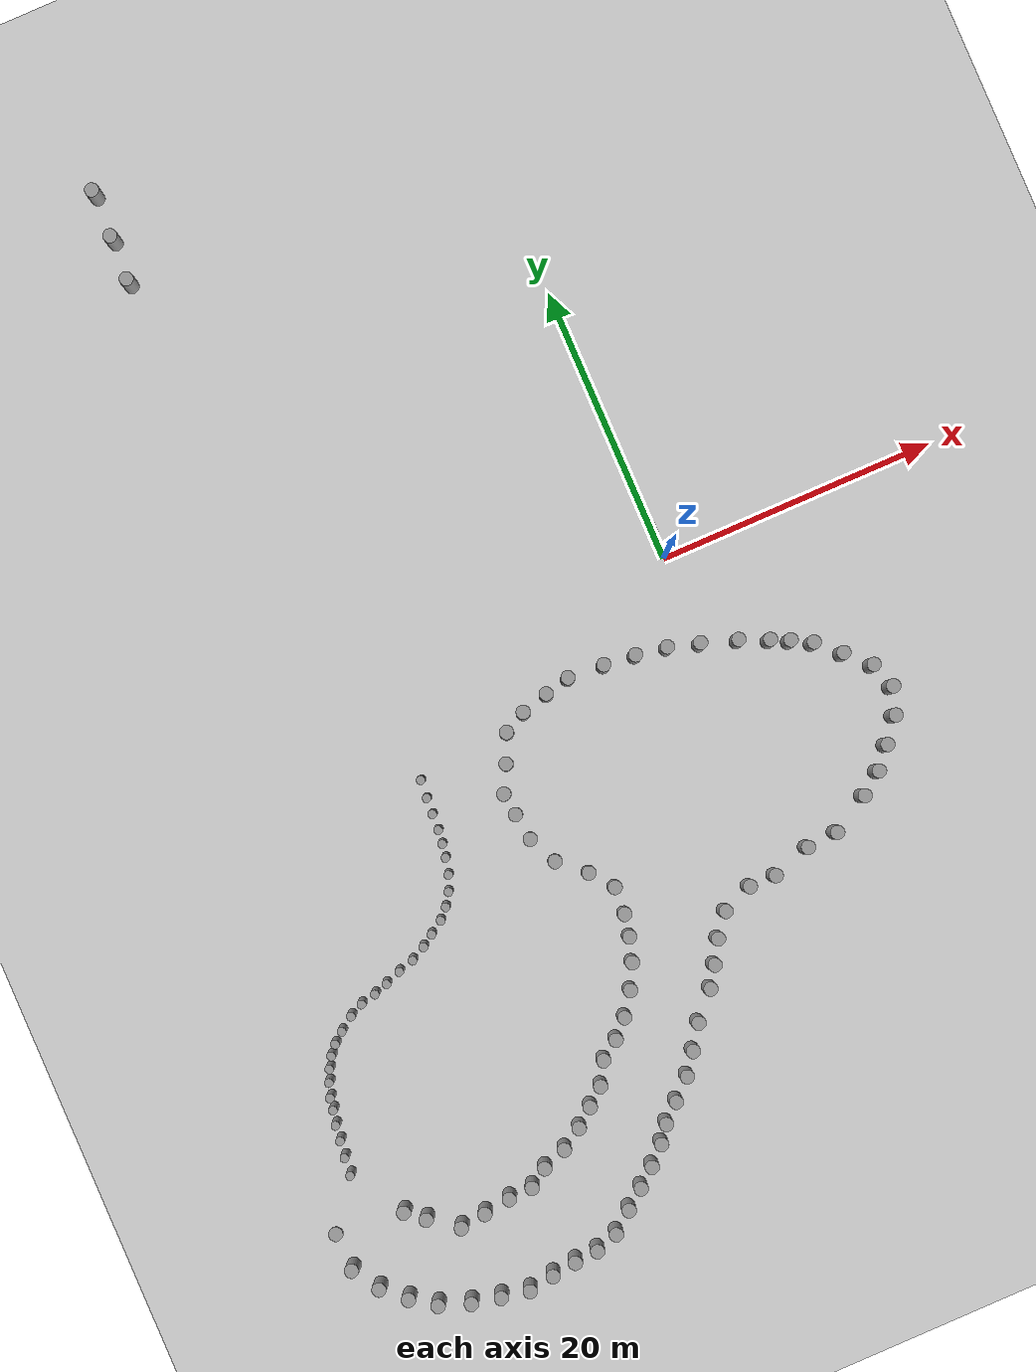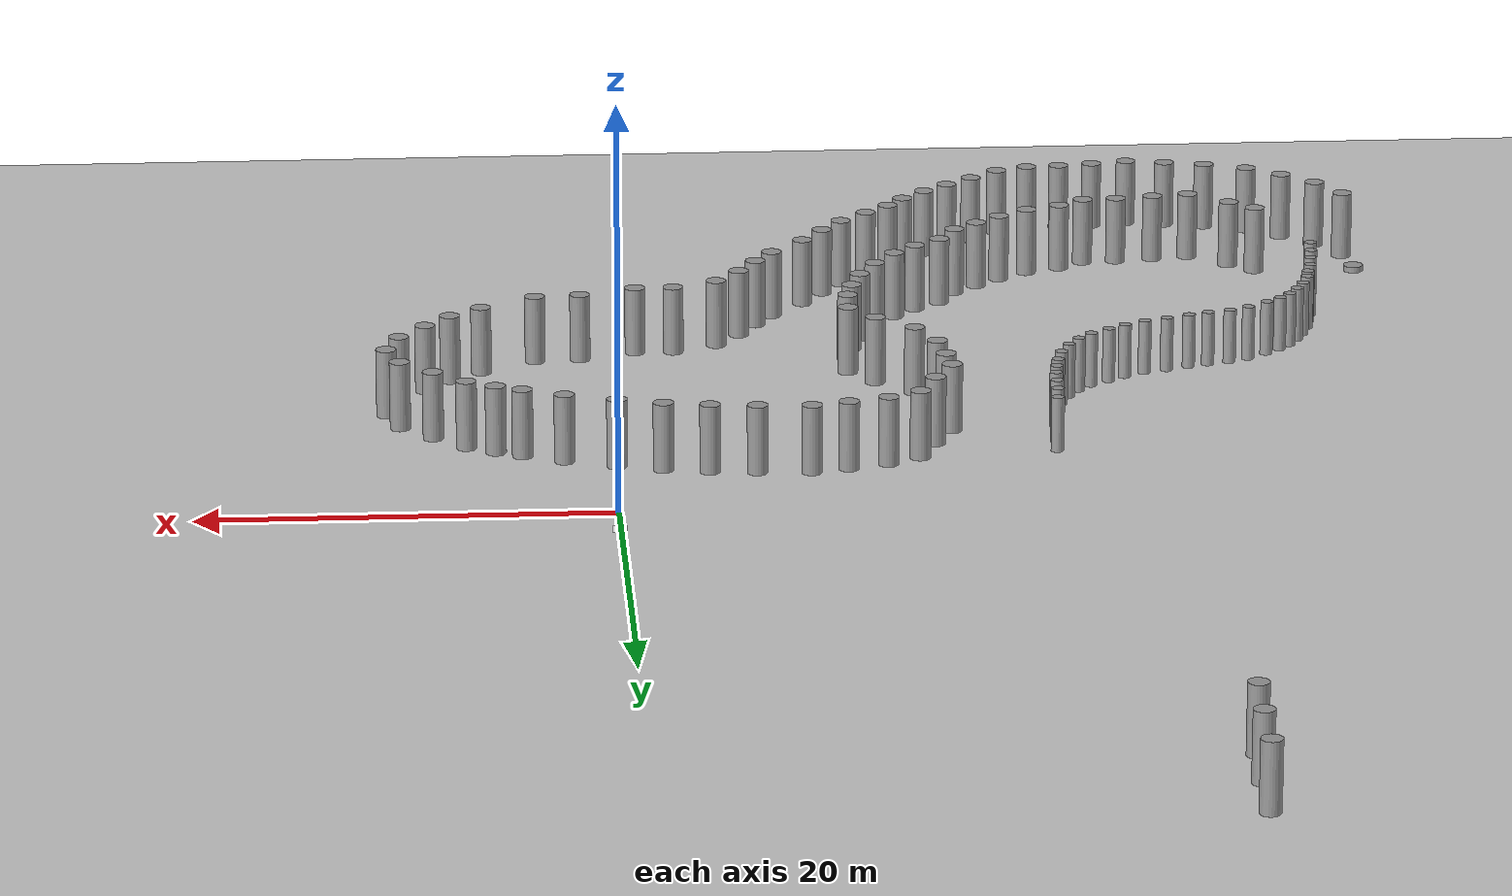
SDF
<sdf version="1.7">
 <world name="default">
  <light name="sun" type="directional">
   <pose>0 0 10 0 -0 0</pose>
   <diffuse>0.8 0.8 0.8 1</diffuse>
   <specular>0.2 0.2 0.2 1</specular>
   <attenuation>
    <range>1000</range>
    <constant>0.9</constant>
    <linear>0.01</linear>
    <quadratic>0.001</quadratic>
   </attenuation>
   <direction>-0.5 0.1 -0.9</direction>
   <spot><inner_angle>0</inner_angle><outer_angle>0</outer_angle><falloff>0</falloff></spot>
  </light>
  <model name="ground_plane">
   <static>1</static>
   <link name="link">
    <collision name="collision">
     <geometry><plane><normal>0 0 1</normal><size>100 100</size></plane></geometry>
     <surface>
      <contact><collide_bitmask>65535</collide_bitmask></contact>
      <friction><ode><mu>100</mu><mu2>50</mu2></ode></friction>
     </surface>
    </collision>
    <visual name="visual">
     <cast_shadows>0</cast_shadows>
     <geometry><plane><normal>0 0 1</normal><size>100 100</size></plane></geometry>
     <material>
      <script><uri>file://media/materials/scripts/gazebo.material</uri><name>Gazebo/Grey</name></script>
     </material>
    </visual>
   </link>
  </model>
  <gravity>0 0 -9.8</gravity>
  <magnetic_field>6e-06 2.3e-05 -4.2e-05</magnetic_field>
  <atmosphere type="adiabatic"/>
  <physics type="ode">
   <max_step_size>0.001</max_step_size>
   <real_time_factor>1</real_time_factor>
   <real_time_update_rate>1000</real_time_update_rate>
  </physics>
  <scene><ambient>0.4 0.4 0.4 1</ambient><background>0.7 0.7 0.7 1</background><shadows>1</shadows></scene>
  <spherical_coordinates>
   <surface_model>EARTH_WGS84</surface_model>
   <latitude_deg>0</latitude_deg>
   <longitude_deg>0</longitude_deg>
   <elevation>0</elevation>
   <heading_deg>0</heading_deg>
  </spherical_coordinates>
  <model name="aruco_default">
   <static>1</static>
   <link name="aruco_link">
    <visual name="aruco_visual">
     <geometry><plane><normal>0 0 1</normal><size>0.68 0.9</size></plane></geometry>
     <material>
      <diffuse>1 1 1 1</diffuse>
      <specular>0.4 0.4 0.4 1</specular>
      <pbr><metal><albedo_map>materials/textures/pattern.png</albedo_map></metal></pbr>
     </material>
    </visual>
   </link>
   <pose>0.057366 2.14573 0 0 -0 0</pose>
  </model>
  <model name="unit_cylinder">
   <pose>-39.2193 -33.7242 0.146396 0 -0 0</pose>
   <link name="link">
    <inertial>
     <mass>1</mass>
     <inertia><ixx>0.145833</ixx><ixy>0</ixy><ixz>0</ixz><iyy>0.145833</iyy><iyz>0</iyz><izz>0.125</izz></inertia>
    </inertial>
    <collision name="collision">
     <geometry><cylinder><radius>0.5</radius><length>0.292792</length></cylinder></geometry>
    </collision>
    <visual name="visual">
     <geometry><cylinder><radius>0.5</radius><length>0.292792</length></cylinder></geometry>
     <material>
      <script><name>Gazebo/Grey</name><uri>file://media/materials/scripts/gazebo.material</uri></script>
     </material>
    </visual>
   </link>
  </model>
  <model name="unit_cylinder_clone">
   <pose>-34.1012 -33.9397 1.7077 0 -0 -2.2e-05</pose>
   <link name="link">
    <inertial>
     <mass>1</mass>
     <inertia><ixx>0.145833</ixx><ixy>0</ixy><ixz>0</ixz><iyy>0.145833</iyy><iyz>0</iyz><izz>0.125</izz></inertia>
    </inertial>
    <collision name="collision">
     <geometry><cylinder><radius>0.5</radius><length>3.4154</length></cylinder></geometry>
    </collision>
    <visual name="visual">
     <geometry><cylinder><radius>0.5</radius><length>3.4154</length></cylinder></geometry>
     <material>
      <script><name>Gazebo/Grey</name><uri>file://media/materials/scripts/gazebo.material</uri></script>
     </material>
    </visual>
   </link>
  </model>
  <model name="unit_cylinder_clone_0">
   <pose>-38.9005 -36.1347 1.7077 0 -0 -3.1e-05</pose>
   <link name="link">
    <inertial>
     <mass>1</mass>
     <inertia><ixx>0.145833</ixx><ixy>0</ixy><ixz>0</ixz><iyy>0.145833</iyy><iyz>0</iyz><izz>0.125</izz></inertia>
    </inertial>
    <collision name="collision">
     <geometry><cylinder><radius>0.5</radius><length>3.4154</length></cylinder></geometry>
    </collision>
    <visual name="visual">
     <geometry><cylinder><radius>0.5</radius><length>3.4154</length></cylinder></geometry>
     <material>
      <script><name>Gazebo/Grey</name><uri>file://media/materials/scripts/gazebo.material</uri></script>
     </material>
    </visual>
   </link>
  </model>
  <model name="unit_cylinder_clone_0_clone">
   <pose>-37.7006 -38.0418 1.7077 0 -0 -3.1e-05</pose>
   <link name="link">
    <inertial>
     <mass>1</mass>
     <inertia><ixx>0.145833</ixx><ixy>0</ixy><ixz>0</ixz><iyy>0.145833</iyy><iyz>0</iyz><izz>0.125</izz></inertia>
    </inertial>
    <collision name="collision">
     <geometry><cylinder><radius>0.5</radius><length>3.4154</length></cylinder></geometry>
    </collision>
    <visual name="visual">
     <geometry><cylinder><radius>0.5</radius><length>3.4154</length></cylinder></geometry>
     <material>
      <script><name>Gazebo/Grey</name><uri>file://media/materials/scripts/gazebo.material</uri></script>
     </material>
    </visual>
   </link>
  </model>
  <model name="unit_cylinder_clone_0_clone_0">
   <pose>-36.1409 -39.4786 1.7077 0 -0 -1.9e-05</pose>
   <link name="link">
    <inertial>
     <mass>1</mass>
     <inertia><ixx>0.145833</ixx><ixy>0</ixy><ixz>0</ixz><iyy>0.145833</iyy><iyz>0</iyz><izz>0.125</izz></inertia>
    </inertial>
    <collision name="collision">
     <geometry><cylinder><radius>0.5</radius><length>3.4154</length></cylinder></geometry>
    </collision>
    <visual name="visual">
     <geometry><cylinder><radius>0.5</radius><length>3.4154</length></cylinder></geometry>
     <material>
      <script><name>Gazebo/Grey</name><uri>file://media/materials/scripts/gazebo.material</uri></script>
     </material>
    </visual>
   </link>
  </model>
  <model name="unit_cylinder_clone_0_clone_1">
   <pose>-32.8781 -34.9904 1.7077 0 -0 -1.7e-05</pose>
   <link name="link">
    <inertial>
     <mass>1</mass>
     <inertia><ixx>0.145833</ixx><ixy>0</ixy><ixz>0</ixz><iyy>0.145833</iyy><iyz>0</iyz><izz>0.125</izz></inertia>
    </inertial>
    <collision name="collision">
     <geometry><cylinder><radius>0.5</radius><length>3.4154</length></cylinder></geometry>
    </collision>
    <visual name="visual">
     <geometry><cylinder><radius>0.5</radius><length>3.4154</length></cylinder></geometry>
     <material>
      <script><name>Gazebo/Grey</name><uri>file://media/materials/scripts/gazebo.material</uri></script>
     </material>
    </visual>
   </link>
  </model>
  <model name="unit_cylinder_clone_0_clone_2">
   <pose>-30.9254 -36.4618 1.7077 0 -0 -3.1e-05</pose>
   <link name="link">
    <inertial>
     <mass>1</mass>
     <inertia><ixx>0.145833</ixx><ixy>0</ixy><ixz>0</ixz><iyy>0.145833</iyy><iyz>0</iyz><izz>0.125</izz></inertia>
    </inertial>
    <collision name="collision">
     <geometry><cylinder><radius>0.5</radius><length>3.4154</length></cylinder></geometry>
    </collision>
    <visual name="visual">
     <geometry><cylinder><radius>0.5</radius><length>3.4154</length></cylinder></geometry>
     <material>
      <script><name>Gazebo/Grey</name><uri>file://media/materials/scripts/gazebo.material</uri></script>
     </material>
    </visual>
   </link>
  </model>
  <model name="unit_cylinder_clone_0_clone_3">
   <pose>-34.4586 -40.6588 1.7077 0 -0 -2.2e-05</pose>
   <link name="link">
    <inertial>
     <mass>1</mass>
     <inertia><ixx>0.145833</ixx><ixy>0</ixy><ixz>0</ixz><iyy>0.145833</iyy><iyz>0</iyz><izz>0.125</izz></inertia>
    </inertial>
    <collision name="collision">
     <geometry><cylinder><radius>0.5</radius><length>3.4154</length></cylinder></geometry>
    </collision>
    <visual name="visual">
     <geometry><cylinder><radius>0.5</radius><length>3.4154</length></cylinder></geometry>
     <material>
      <script><name>Gazebo/Grey</name><uri>file://media/materials/scripts/gazebo.material</uri></script>
     </material>
    </visual>
   </link>
  </model>
  <model name="unit_cylinder_clone_0_clone_4">
   <pose>-32.3305 -41.4258 1.7077 0 -0 -2.3e-05</pose>
   <link name="link">
    <inertial>
     <mass>1</mass>
     <inertia><ixx>0.145833</ixx><ixy>0</ixy><ixz>0</ixz><iyy>0.145833</iyy><iyz>0</iyz><izz>0.125</izz></inertia>
    </inertial>
    <collision name="collision">
     <geometry><cylinder><radius>0.5</radius><length>3.4154</length></cylinder></geometry>
    </collision>
    <visual name="visual">
     <geometry><cylinder><radius>0.5</radius><length>3.4154</length></cylinder></geometry>
     <material>
      <script><name>Gazebo/Grey</name><uri>file://media/materials/scripts/gazebo.material</uri></script>
     </material>
    </visual>
   </link>
  </model>
  <model name="unit_cylinder_clone_0_clone_5">
   <pose>-30.3061 -41.8642 1.7077 0 -0 -1.5e-05</pose>
   <link name="link">
    <inertial>
     <mass>1</mass>
     <inertia><ixx>0.145833</ixx><ixy>0</ixy><ixz>0</ixz><iyy>0.145833</iyy><iyz>0</iyz><izz>0.125</izz></inertia>
    </inertial>
    <collision name="collision">
     <geometry><cylinder><radius>0.5</radius><length>3.4154</length></cylinder></geometry>
    </collision>
    <visual name="visual">
     <geometry><cylinder><radius>0.5</radius><length>3.4154</length></cylinder></geometry>
     <material>
      <script><name>Gazebo/Grey</name><uri>file://media/materials/scripts/gazebo.material</uri></script>
     </material>
    </visual>
   </link>
  </model>
  <model name="unit_cylinder_clone_0_clone_6">
   <pose>-29.0788 -36.2182 1.7077 0 -0 -1.5e-05</pose>
   <link name="link">
    <inertial>
     <mass>1</mass>
     <inertia><ixx>0.145833</ixx><ixy>0</ixy><ixz>0</ixz><iyy>0.145833</iyy><iyz>0</iyz><izz>0.125</izz></inertia>
    </inertial>
    <collision name="collision">
     <geometry><cylinder><radius>0.5</radius><length>3.4154</length></cylinder></geometry>
    </collision>
    <visual name="visual">
     <geometry><cylinder><radius>0.5</radius><length>3.4154</length></cylinder></geometry>
     <material>
      <script><name>Gazebo/Grey</name><uri>file://media/materials/scripts/gazebo.material</uri></script>
     </material>
    </visual>
   </link>
  </model>
  <model name="unit_cylinder_clone_0_clone_7">
   <pose>-27.1603 -35.9543 1.7077 0 -0 -1.5e-05</pose>
   <link name="link">
    <inertial>
     <mass>1</mass>
     <inertia><ixx>0.145833</ixx><ixy>0</ixy><ixz>0</ixz><iyy>0.145833</iyy><iyz>0</iyz><izz>0.125</izz></inertia>
    </inertial>
    <collision name="collision">
     <geometry><cylinder><radius>0.5</radius><length>3.4154</length></cylinder></geometry>
    </collision>
    <visual name="visual">
     <geometry><cylinder><radius>0.5</radius><length>3.4154</length></cylinder></geometry>
     <material>
      <script><name>Gazebo/Grey</name><uri>file://media/materials/scripts/gazebo.material</uri></script>
     </material>
    </visual>
   </link>
  </model>
  <model name="unit_cylinder_clone_0_clone_8">
   <pose>-28.3277 -42.2291 1.7077 0 -0 -1.5e-05</pose>
   <link name="link">
    <inertial>
     <mass>1</mass>
     <inertia><ixx>0.145833</ixx><ixy>0</ixy><ixz>0</ixz><iyy>0.145833</iyy><iyz>0</iyz><izz>0.125</izz></inertia>
    </inertial>
    <collision name="collision">
     <geometry><cylinder><radius>0.5</radius><length>3.4154</length></cylinder></geometry>
    </collision>
    <visual name="visual">
     <geometry><cylinder><radius>0.5</radius><length>3.4154</length></cylinder></geometry>
     <material>
      <script><name>Gazebo/Grey</name><uri>file://media/materials/scripts/gazebo.material</uri></script>
     </material>
    </visual>
   </link>
  </model>
  <model name="unit_cylinder_clone_0_clone_9">
   <pose>-26.4941 -41.9155 1.7077 0 -0 -3.1e-05</pose>
   <link name="link">
    <inertial>
     <mass>1</mass>
     <inertia><ixx>0.145833</ixx><ixy>0</ixy><ixz>0</ixz><iyy>0.145833</iyy><iyz>0</iyz><izz>0.125</izz></inertia>
    </inertial>
    <collision name="collision">
     <geometry><cylinder><radius>0.5</radius><length>3.4154</length></cylinder></geometry>
    </collision>
    <visual name="visual">
     <geometry><cylinder><radius>0.5</radius><length>3.4154</length></cylinder></geometry>
     <material>
      <script><name>Gazebo/Grey</name><uri>file://media/materials/scripts/gazebo.material</uri></script>
     </material>
    </visual>
   </link>
  </model>
  <model name="unit_cylinder_clone_0_clone_10">
   <pose>-25.4379 -35.8604 1.7077 0 -0 -1.5e-05</pose>
   <link name="link">
    <inertial>
     <mass>1</mass>
     <inertia><ixx>0.145833</ixx><ixy>0</ixy><ixz>0</ixz><iyy>0.145833</iyy><iyz>0</iyz><izz>0.125</izz></inertia>
    </inertial>
    <collision name="collision">
     <geometry><cylinder><radius>0.5</radius><length>3.4154</length></cylinder></geometry>
    </collision>
    <visual name="visual">
     <geometry><cylinder><radius>0.5</radius><length>3.4154</length></cylinder></geometry>
     <material>
      <script><name>Gazebo/Grey</name><uri>file://media/materials/scripts/gazebo.material</uri></script>
     </material>
    </visual>
   </link>
  </model>
  <model name="unit_cylinder_clone_0_clone_11">
   <pose>-24.7496 -41.6817 1.7077 0 -0 -1.5e-05</pose>
   <link name="link">
    <inertial>
     <mass>1</mass>
     <inertia><ixx>0.145833</ixx><ixy>0</ixy><ixz>0</ixz><iyy>0.145833</iyy><iyz>0</iyz><izz>0.125</izz></inertia>
    </inertial>
    <collision name="collision">
     <geometry><cylinder><radius>0.5</radius><length>3.4154</length></cylinder></geometry>
    </collision>
    <visual name="visual">
     <geometry><cylinder><radius>0.5</radius><length>3.4154</length></cylinder></geometry>
     <material>
      <script><name>Gazebo/Grey</name><uri>file://media/materials/scripts/gazebo.material</uri></script>
     </material>
    </visual>
   </link>
  </model>
  <model name="unit_cylinder_clone_0_clone_12">
   <pose>-24.1228 -34.9902 1.7077 0 -0 -3.1e-05</pose>
   <link name="link">
    <inertial>
     <mass>1</mass>
     <inertia><ixx>0.145833</ixx><ixy>0</ixy><ixz>0</ixz><iyy>0.145833</iyy><iyz>0</iyz><izz>0.125</izz></inertia>
    </inertial>
    <collision name="collision">
     <geometry><cylinder><radius>0.5</radius><length>3.4154</length></cylinder></geometry>
    </collision>
    <visual name="visual">
     <geometry><cylinder><radius>0.5</radius><length>3.4154</length></cylinder></geometry>
     <material>
      <script><name>Gazebo/Grey</name><uri>file://media/materials/scripts/gazebo.material</uri></script>
     </material>
    </visual>
   </link>
  </model>
  <model name="unit_cylinder_clone_0_clone_13">
   <pose>-23.0668 -41.5626 1.7077 0 -0 -1.5e-05</pose>
   <link name="link">
    <inertial>
     <mass>1</mass>
     <inertia><ixx>0.145833</ixx><ixy>0</ixy><ixz>0</ixz><iyy>0.145833</iyy><iyz>0</iyz><izz>0.125</izz></inertia>
    </inertial>
    <collision name="collision">
     <geometry><cylinder><radius>0.5</radius><length>3.4154</length></cylinder></geometry>
    </collision>
    <visual name="visual">
     <geometry><cylinder><radius>0.5</radius><length>3.4154</length></cylinder></geometry>
     <material>
      <script><name>Gazebo/Grey</name><uri>file://media/materials/scripts/gazebo.material</uri></script>
     </material>
    </visual>
   </link>
  </model>
  <model name="unit_cylinder_clone_0_clone_14">
   <pose>-21.4401 -41.0301 1.7077 0 -0 -1.5e-05</pose>
   <link name="link">
    <inertial>
     <mass>1</mass>
     <inertia><ixx>0.145833</ixx><ixy>0</ixy><ixz>0</ixz><iyy>0.145833</iyy><iyz>0</iyz><izz>0.125</izz></inertia>
    </inertial>
    <collision name="collision">
     <geometry><cylinder><radius>0.5</radius><length>3.4154</length></cylinder></geometry>
    </collision>
    <visual name="visual">
     <geometry><cylinder><radius>0.5</radius><length>3.4154</length></cylinder></geometry>
     <material>
      <script><name>Gazebo/Grey</name><uri>file://media/materials/scripts/gazebo.material</uri></script>
     </material>
    </visual>
   </link>
  </model>
  <model name="unit_cylinder_clone_0_clone_15">
   <pose>-22.3934 -34.3642 1.7077 0 -0 -1.5e-05</pose>
   <link name="link">
    <inertial>
     <mass>1</mass>
     <inertia><ixx>0.145833</ixx><ixy>0</ixy><ixz>0</ixz><iyy>0.145833</iyy><iyz>0</iyz><izz>0.125</izz></inertia>
    </inertial>
    <collision name="collision">
     <geometry><cylinder><radius>0.5</radius><length>3.4154</length></cylinder></geometry>
    </collision>
    <visual name="visual">
     <geometry><cylinder><radius>0.5</radius><length>3.4154</length></cylinder></geometry>
     <material>
      <script><name>Gazebo/Grey</name><uri>file://media/materials/scripts/gazebo.material</uri></script>
     </material>
    </visual>
   </link>
  </model>
  <model name="unit_cylinder_clone_0_clone_16">
   <pose>-19.9972 -39.8775 1.7077 0 -0 -1.5e-05</pose>
   <link name="link">
    <inertial>
     <mass>1</mass>
     <inertia><ixx>0.145833</ixx><ixy>0</ixy><ixz>0</ixz><iyy>0.145833</iyy><iyz>0</iyz><izz>0.125</izz></inertia>
    </inertial>
    <collision name="collision">
     <geometry><cylinder><radius>0.5</radius><length>3.4154</length></cylinder></geometry>
    </collision>
    <visual name="visual">
     <geometry><cylinder><radius>0.5</radius><length>3.4154</length></cylinder></geometry>
     <material>
      <script><name>Gazebo/Grey</name><uri>file://media/materials/scripts/gazebo.material</uri></script>
     </material>
    </visual>
   </link>
  </model>
  <model name="unit_cylinder_clone_0_clone_17">
   <pose>-18.657 -38.8392 1.7077 0 -0 -3.1e-05</pose>
   <link name="link">
    <inertial>
     <mass>1</mass>
     <inertia><ixx>0.145833</ixx><ixy>0</ixy><ixz>0</ixz><iyy>0.145833</iyy><iyz>0</iyz><izz>0.125</izz></inertia>
    </inertial>
    <collision name="collision">
     <geometry><cylinder><radius>0.5</radius><length>3.4154</length></cylinder></geometry>
    </collision>
    <visual name="visual">
     <geometry><cylinder><radius>0.5</radius><length>3.4154</length></cylinder></geometry>
     <material>
      <script><name>Gazebo/Grey</name><uri>file://media/materials/scripts/gazebo.material</uri></script>
     </material>
    </visual>
   </link>
  </model>
  <model name="unit_cylinder_clone_0_clone_18">
   <pose>-20.8912 -33.4203 1.7077 0 -0 -3.1e-05</pose>
   <link name="link">
    <inertial>
     <mass>1</mass>
     <inertia><ixx>0.145833</ixx><ixy>0</ixy><ixz>0</ixz><iyy>0.145833</iyy><iyz>0</iyz><izz>0.125</izz></inertia>
    </inertial>
    <collision name="collision">
     <geometry><cylinder><radius>0.5</radius><length>3.4154</length></cylinder></geometry>
    </collision>
    <visual name="visual">
     <geometry><cylinder><radius>0.5</radius><length>3.4154</length></cylinder></geometry>
     <material>
      <script><name>Gazebo/Grey</name><uri>file://media/materials/scripts/gazebo.material</uri></script>
     </material>
    </visual>
   </link>
  </model>
  <model name="unit_cylinder_clone_0_clone_19">
   <pose>-17.3958 -37.8043 1.7077 0 -0 -1.5e-05</pose>
   <link name="link">
    <inertial>
     <mass>1</mass>
     <inertia><ixx>0.145833</ixx><ixy>0</ixy><ixz>0</ixz><iyy>0.145833</iyy><iyz>0</iyz><izz>0.125</izz></inertia>
    </inertial>
    <collision name="collision">
     <geometry><cylinder><radius>0.5</radius><length>3.4154</length></cylinder></geometry>
    </collision>
    <visual name="visual">
     <geometry><cylinder><radius>0.5</radius><length>3.4154</length></cylinder></geometry>
     <material>
      <script><name>Gazebo/Grey</name><uri>file://media/materials/scripts/gazebo.material</uri></script>
     </material>
    </visual>
   </link>
  </model>
  <model name="unit_cylinder_clone_0_clone_20">
   <pose>-19.6384 -32.4055 1.7077 0 -0 -3e-05</pose>
   <link name="link">
    <inertial>
     <mass>1</mass>
     <inertia><ixx>0.145833</ixx><ixy>0</ixy><ixz>0</ixz><iyy>0.145833</iyy><iyz>0</iyz><izz>0.125</izz></inertia>
    </inertial>
    <collision name="collision">
     <geometry><cylinder><radius>0.5</radius><length>3.4154</length></cylinder></geometry>
    </collision>
    <visual name="visual">
     <geometry><cylinder><radius>0.5</radius><length>3.4154</length></cylinder></geometry>
     <material>
      <script><name>Gazebo/Grey</name><uri>file://media/materials/scripts/gazebo.material</uri></script>
     </material>
    </visual>
   </link>
  </model>
  <model name="unit_cylinder_clone_0_clone_21">
   <pose>-16.1906 -36.6426 1.7077 0 -0 -6e-06</pose>
   <link name="link">
    <inertial>
     <mass>1</mass>
     <inertia><ixx>0.145833</ixx><ixy>0</ixy><ixz>0</ixz><iyy>0.145833</iyy><iyz>0</iyz><izz>0.125</izz></inertia>
    </inertial>
    <collision name="collision">
     <geometry><cylinder><radius>0.5</radius><length>3.4154</length></cylinder></geometry>
    </collision>
    <visual name="visual">
     <geometry><cylinder><radius>0.5</radius><length>3.4154</length></cylinder></geometry>
     <material>
      <script><name>Gazebo/Grey</name><uri>file://media/materials/scripts/gazebo.material</uri></script>
     </material>
    </visual>
   </link>
  </model>
  <model name="unit_cylinder_clone_0_clone_22">
   <pose>-15.3446 -35.5243 1.7077 0 -0 -7e-06</pose>
   <link name="link">
    <inertial>
     <mass>1</mass>
     <inertia><ixx>0.145833</ixx><ixy>0</ixy><ixz>0</ixz><iyy>0.145833</iyy><iyz>0</iyz><izz>0.125</izz></inertia>
    </inertial>
    <collision name="collision">
     <geometry><cylinder><radius>0.5</radius><length>3.4154</length></cylinder></geometry>
    </collision>
    <visual name="visual">
     <geometry><cylinder><radius>0.5</radius><length>3.4154</length></cylinder></geometry>
     <material>
      <script><name>Gazebo/Grey</name><uri>file://media/materials/scripts/gazebo.material</uri></script>
     </material>
    </visual>
   </link>
  </model>
  <model name="unit_cylinder_clone_0_clone_23">
   <pose>-18.432 -31.4004 1.7077 0 -0 -3.5e-05</pose>
   <link name="link">
    <inertial>
     <mass>1</mass>
     <inertia><ixx>0.145833</ixx><ixy>0</ixy><ixz>0</ixz><iyy>0.145833</iyy><iyz>0</iyz><izz>0.125</izz></inertia>
    </inertial>
    <collision name="collision">
     <geometry><cylinder><radius>0.5</radius><length>3.4154</length></cylinder></geometry>
    </collision>
    <visual name="visual">
     <geometry><cylinder><radius>0.5</radius><length>3.4154</length></cylinder></geometry>
     <material>
      <script><name>Gazebo/Grey</name><uri>file://media/materials/scripts/gazebo.material</uri></script>
     </material>
    </visual>
   </link>
  </model>
  <model name="unit_cylinder_clone_0_clone_24">
   <pose>-17.5365 -29.8651 1.7077 0 -0 -3.5e-05</pose>
   <link name="link">
    <inertial>
     <mass>1</mass>
     <inertia><ixx>0.145833</ixx><ixy>0</ixy><ixz>0</ixz><iyy>0.145833</iyy><iyz>0</iyz><izz>0.125</izz></inertia>
    </inertial>
    <collision name="collision">
     <geometry><cylinder><radius>0.5</radius><length>3.4154</length></cylinder></geometry>
    </collision>
    <visual name="visual">
     <geometry><cylinder><radius>0.5</radius><length>3.4154</length></cylinder></geometry>
     <material>
      <script><name>Gazebo/Grey</name><uri>file://media/materials/scripts/gazebo.material</uri></script>
     </material>
    </visual>
   </link>
  </model>
  <model name="unit_cylinder_clone_0_clone_25">
   <pose>-14.135 -34.4155 1.7077 0 -0 -1.8e-05</pose>
   <link name="link">
    <inertial>
     <mass>1</mass>
     <inertia><ixx>0.145833</ixx><ixy>0</ixy><ixz>0</ixz><iyy>0.145833</iyy><iyz>0</iyz><izz>0.125</izz></inertia>
    </inertial>
    <collision name="collision">
     <geometry><cylinder><radius>0.5</radius><length>3.4154</length></cylinder></geometry>
    </collision>
    <visual name="visual">
     <geometry><cylinder><radius>0.5</radius><length>3.4154</length></cylinder></geometry>
     <material>
      <script><name>Gazebo/Grey</name><uri>file://media/materials/scripts/gazebo.material</uri></script>
     </material>
    </visual>
   </link>
  </model>
  <model name="unit_cylinder_clone_0_clone_26">
   <pose>-12.7615 -33.134 1.7077 0 -0 -1.8e-05</pose>
   <link name="link">
    <inertial>
     <mass>1</mass>
     <inertia><ixx>0.145833</ixx><ixy>0</ixy><ixz>0</ixz><iyy>0.145833</iyy><iyz>0</iyz><izz>0.125</izz></inertia>
    </inertial>
    <collision name="collision">
     <geometry><cylinder><radius>0.5</radius><length>3.4154</length></cylinder></geometry>
    </collision>
    <visual name="visual">
     <geometry><cylinder><radius>0.5</radius><length>3.4154</length></cylinder></geometry>
     <material>
      <script><name>Gazebo/Grey</name><uri>file://media/materials/scripts/gazebo.material</uri></script>
     </material>
    </visual>
   </link>
  </model>
  <model name="unit_cylinder_clone_0_clone_27">
   <pose>-11.7056 -31.7164 1.7077 0 -0 -1.1e-05</pose>
   <link name="link">
    <inertial>
     <mass>1</mass>
     <inertia><ixx>0.145833</ixx><ixy>0</ixy><ixz>0</ixz><iyy>0.145833</iyy><iyz>0</iyz><izz>0.125</izz></inertia>
    </inertial>
    <collision name="collision">
     <geometry><cylinder><radius>0.5</radius><length>3.4154</length></cylinder></geometry>
    </collision>
    <visual name="visual">
     <geometry><cylinder><radius>0.5</radius><length>3.4154</length></cylinder></geometry>
     <material>
      <script><name>Gazebo/Grey</name><uri>file://media/materials/scripts/gazebo.material</uri></script>
     </material>
    </visual>
   </link>
  </model>
  <model name="unit_cylinder_clone_0_clone_28">
   <pose>-10.5947 -30.1055 1.7077 0 -0 -2.6e-05</pose>
   <link name="link">
    <inertial>
     <mass>1</mass>
     <inertia><ixx>0.145833</ixx><ixy>0</ixy><ixz>0</ixz><iyy>0.145833</iyy><iyz>0</iyz><izz>0.125</izz></inertia>
    </inertial>
    <collision name="collision">
     <geometry><cylinder><radius>0.5</radius><length>3.4154</length></cylinder></geometry>
    </collision>
    <visual name="visual">
     <geometry><cylinder><radius>0.5</radius><length>3.4154</length></cylinder></geometry>
     <material>
      <script><name>Gazebo/Grey</name><uri>file://media/materials/scripts/gazebo.material</uri></script>
     </material>
    </visual>
   </link>
  </model>
  <model name="unit_cylinder_clone_0_clone_29">
   <pose>-8.92083 -28.3016 1.7077 0 -0 -7e-06</pose>
   <link name="link">
    <inertial>
     <mass>1</mass>
     <inertia><ixx>0.145833</ixx><ixy>0</ixy><ixz>0</ixz><iyy>0.145833</iyy><iyz>0</iyz><izz>0.125</izz></inertia>
    </inertial>
    <collision name="collision">
     <geometry><cylinder><radius>0.5</radius><length>3.4154</length></cylinder></geometry>
    </collision>
    <visual name="visual">
     <geometry><cylinder><radius>0.5</radius><length>3.4154</length></cylinder></geometry>
     <material>
      <script><name>Gazebo/Grey</name><uri>file://media/materials/scripts/gazebo.material</uri></script>
     </material>
    </visual>
   </link>
  </model>
  <model name="unit_cylinder_clone_0_clone_30">
   <pose>-16.2133 -28.921 1.7077 0 -0 -9e-06</pose>
   <link name="link">
    <inertial>
     <mass>1</mass>
     <inertia><ixx>0.145833</ixx><ixy>0</ixy><ixz>0</ixz><iyy>0.145833</iyy><iyz>0</iyz><izz>0.125</izz></inertia>
    </inertial>
    <collision name="collision">
     <geometry><cylinder><radius>0.5</radius><length>3.4154</length></cylinder></geometry>
    </collision>
    <visual name="visual">
     <geometry><cylinder><radius>0.5</radius><length>3.4154</length></cylinder></geometry>
     <material>
      <script><name>Gazebo/Grey</name><uri>file://media/materials/scripts/gazebo.material</uri></script>
     </material>
    </visual>
   </link>
  </model>
  <model name="unit_cylinder_clone_0_clone_31">
   <pose>-15.0737 -27.7686 1.7077 0 -0 -7e-06</pose>
   <link name="link">
    <inertial>
     <mass>1</mass>
     <inertia><ixx>0.145833</ixx><ixy>0</ixy><ixz>0</ixz><iyy>0.145833</iyy><iyz>0</iyz><izz>0.125</izz></inertia>
    </inertial>
    <collision name="collision">
     <geometry><cylinder><radius>0.5</radius><length>3.4154</length></cylinder></geometry>
    </collision>
    <visual name="visual">
     <geometry><cylinder><radius>0.5</radius><length>3.4154</length></cylinder></geometry>
     <material>
      <script><name>Gazebo/Grey</name><uri>file://media/materials/scripts/gazebo.material</uri></script>
     </material>
    </visual>
   </link>
  </model>
  <model name="unit_cylinder_clone_0_clone_32">
   <pose>-13.9781 -26.2226 1.7077 0 -0 -7e-06</pose>
   <link name="link">
    <inertial>
     <mass>1</mass>
     <inertia><ixx>0.145833</ixx><ixy>0</ixy><ixz>0</ixz><iyy>0.145833</iyy><iyz>0</iyz><izz>0.125</izz></inertia>
    </inertial>
    <collision name="collision">
     <geometry><cylinder><radius>0.5</radius><length>3.4154</length></cylinder></geometry>
    </collision>
    <visual name="visual">
     <geometry><cylinder><radius>0.5</radius><length>3.4154</length></cylinder></geometry>
     <material>
      <script><name>Gazebo/Grey</name><uri>file://media/materials/scripts/gazebo.material</uri></script>
     </material>
    </visual>
   </link>
  </model>
  <model name="unit_cylinder_clone_0_clone_33">
   <pose>-13.1083 -24.5379 1.7077 0 -0 -2.6e-05</pose>
   <link name="link">
    <inertial>
     <mass>1</mass>
     <inertia><ixx>0.145833</ixx><ixy>0</ixy><ixz>0</ixz><iyy>0.145833</iyy><iyz>0</iyz><izz>0.125</izz></inertia>
    </inertial>
    <collision name="collision">
     <geometry><cylinder><radius>0.5</radius><length>3.4154</length></cylinder></geometry>
    </collision>
    <visual name="visual">
     <geometry><cylinder><radius>0.5</radius><length>3.4154</length></cylinder></geometry>
     <material>
      <script><name>Gazebo/Grey</name><uri>file://media/materials/scripts/gazebo.material</uri></script>
     </material>
    </visual>
   </link>
  </model>
  <model name="unit_cylinder_clone_0_clone_34">
   <pose>-12.5767 -22.8633 1.7077 -0 -0 -0.001813</pose>
   <link name="link">
    <inertial>
     <mass>1</mass>
     <inertia><ixx>0.145833</ixx><ixy>0</ixy><ixz>0</ixz><iyy>0.145833</iyy><iyz>0</iyz><izz>0.125</izz></inertia>
    </inertial>
    <collision name="collision">
     <geometry><cylinder><radius>0.5</radius><length>3.4154</length></cylinder></geometry>
    </collision>
    <visual name="visual">
     <geometry><cylinder><radius>0.5</radius><length>3.4154</length></cylinder></geometry>
     <material>
      <script><name>Gazebo/Grey</name><uri>file://media/materials/scripts/gazebo.material</uri></script>
     </material>
    </visual>
   </link>
  </model>
  <model name="unit_cylinder_clone_0_clone_35">
   <pose>-8.01693 -26.923 1.7077 0 -0 -1.7e-05</pose>
   <link name="link">
    <inertial>
     <mass>1</mass>
     <inertia><ixx>0.145833</ixx><ixy>0</ixy><ixz>0</ixz><iyy>0.145833</iyy><iyz>0</iyz><izz>0.125</izz></inertia>
    </inertial>
    <collision name="collision">
     <geometry><cylinder><radius>0.5</radius><length>3.4154</length></cylinder></geometry>
    </collision>
    <visual name="visual">
     <geometry><cylinder><radius>0.5</radius><length>3.4154</length></cylinder></geometry>
     <material>
      <script><name>Gazebo/Grey</name><uri>file://media/materials/scripts/gazebo.material</uri></script>
     </material>
    </visual>
   </link>
  </model>
  <model name="unit_cylinder_clone_0_clone_36">
   <pose>-7.09433 -25.3866 1.7077 0 -0 -2.3e-05</pose>
   <link name="link">
    <inertial>
     <mass>1</mass>
     <inertia><ixx>0.145833</ixx><ixy>0</ixy><ixz>0</ixz><iyy>0.145833</iyy><iyz>0</iyz><izz>0.125</izz></inertia>
    </inertial>
    <collision name="collision">
     <geometry><cylinder><radius>0.5</radius><length>3.4154</length></cylinder></geometry>
    </collision>
    <visual name="visual">
     <geometry><cylinder><radius>0.5</radius><length>3.4154</length></cylinder></geometry>
     <material>
      <script><name>Gazebo/Grey</name><uri>file://media/materials/scripts/gazebo.material</uri></script>
     </material>
    </visual>
   </link>
  </model>
  <model name="unit_cylinder_clone_0_clone_37">
   <pose>-12.2662 -21.3267 1.7077 0 -0 -7e-06</pose>
   <link name="link">
    <inertial>
     <mass>1</mass>
     <inertia><ixx>0.145833</ixx><ixy>0</ixy><ixz>0</ixz><iyy>0.145833</iyy><iyz>0</iyz><izz>0.125</izz></inertia>
    </inertial>
    <collision name="collision">
     <geometry><cylinder><radius>0.5</radius><length>3.4154</length></cylinder></geometry>
    </collision>
    <visual name="visual">
     <geometry><cylinder><radius>0.5</radius><length>3.4154</length></cylinder></geometry>
     <material>
      <script><name>Gazebo/Grey</name><uri>file://media/materials/scripts/gazebo.material</uri></script>
     </material>
    </visual>
   </link>
  </model>
  <model name="unit_cylinder_clone_0_clone_38">
   <pose>-5.87449 -23.8777 1.7077 0 -0 -2.3e-05</pose>
   <link name="link">
    <inertial>
     <mass>1</mass>
     <inertia><ixx>0.145833</ixx><ixy>0</ixy><ixz>0</ixz><iyy>0.145833</iyy><iyz>0</iyz><izz>0.125</izz></inertia>
    </inertial>
    <collision name="collision">
     <geometry><cylinder><radius>0.5</radius><length>3.4154</length></cylinder></geometry>
    </collision>
    <visual name="visual">
     <geometry><cylinder><radius>0.5</radius><length>3.4154</length></cylinder></geometry>
     <material>
      <script><name>Gazebo/Grey</name><uri>file://media/materials/scripts/gazebo.material</uri></script>
     </material>
    </visual>
   </link>
  </model>
  <model name="unit_cylinder_clone_0_clone_39">
   <pose>-12.1496 -19.3923 1.7077 0 -0 -2.6e-05</pose>
   <link name="link">
    <inertial>
     <mass>1</mass>
     <inertia><ixx>0.145833</ixx><ixy>0</ixy><ixz>0</ixz><iyy>0.145833</iyy><iyz>0</iyz><izz>0.125</izz></inertia>
    </inertial>
    <collision name="collision">
     <geometry><cylinder><radius>0.5</radius><length>3.4154</length></cylinder></geometry>
    </collision>
    <visual name="visual">
     <geometry><cylinder><radius>0.5</radius><length>3.4154</length></cylinder></geometry>
     <material>
      <script><name>Gazebo/Grey</name><uri>file://media/materials/scripts/gazebo.material</uri></script>
     </material>
    </visual>
   </link>
  </model>
  <model name="unit_cylinder_clone_0_clone_40">
   <pose>-3.69067 -22.991 1.7077 0 -0 -3.5e-05</pose>
   <link name="link">
    <inertial>
     <mass>1</mass>
     <inertia><ixx>0.145833</ixx><ixy>0</ixy><ixz>0</ixz><iyy>0.145833</iyy><iyz>0</iyz><izz>0.125</izz></inertia>
    </inertial>
    <collision name="collision">
     <geometry><cylinder><radius>0.5</radius><length>3.4154</length></cylinder></geometry>
    </collision>
    <visual name="visual">
     <geometry><cylinder><radius>0.5</radius><length>3.4154</length></cylinder></geometry>
     <material>
      <script><name>Gazebo/Grey</name><uri>file://media/materials/scripts/gazebo.material</uri></script>
     </material>
    </visual>
   </link>
  </model>
  <model name="unit_cylinder_clone_0_clone_41">
   <pose>-1.78617 -23.0066 1.7077 0 -0 -1.1e-05</pose>
   <link name="link">
    <inertial>
     <mass>1</mass>
     <inertia><ixx>0.145833</ixx><ixy>0</ixy><ixz>0</ixz><iyy>0.145833</iyy><iyz>0</iyz><izz>0.125</izz></inertia>
    </inertial>
    <collision name="collision">
     <geometry><cylinder><radius>0.5</radius><length>3.4154</length></cylinder></geometry>
    </collision>
    <visual name="visual">
     <geometry><cylinder><radius>0.5</radius><length>3.4154</length></cylinder></geometry>
     <material>
      <script><name>Gazebo/Grey</name><uri>file://media/materials/scripts/gazebo.material</uri></script>
     </material>
    </visual>
   </link>
  </model>
  <model name="unit_cylinder_clone_0_clone_42">
   <pose>0.987359 -22.1201 1.7077 0 -0 -2.1e-05</pose>
   <link name="link">
    <inertial>
     <mass>1</mass>
     <inertia><ixx>0.145833</ixx><ixy>0</ixy><ixz>0</ixz><iyy>0.145833</iyy><iyz>0</iyz><izz>0.125</izz></inertia>
    </inertial>
    <collision name="collision">
     <geometry><cylinder><radius>0.5</radius><length>3.4154</length></cylinder></geometry>
    </collision>
    <visual name="visual">
     <geometry><cylinder><radius>0.5</radius><length>3.4154</length></cylinder></geometry>
     <material>
      <script><name>Gazebo/Grey</name><uri>file://media/materials/scripts/gazebo.material</uri></script>
     </material>
    </visual>
   </link>
  </model>
  <model name="unit_cylinder_clone_0_clone_43">
   <pose>-13.3909 -17.7902 1.7077 0 -0 -7e-06</pose>
   <link name="link">
    <inertial>
     <mass>1</mass>
     <inertia><ixx>0.145833</ixx><ixy>0</ixy><ixz>0</ixz><iyy>0.145833</iyy><iyz>0</iyz><izz>0.125</izz></inertia>
    </inertial>
    <collision name="collision">
     <geometry><cylinder><radius>0.5</radius><length>3.4154</length></cylinder></geometry>
    </collision>
    <visual name="visual">
     <geometry><cylinder><radius>0.5</radius><length>3.4154</length></cylinder></geometry>
     <material>
      <script><name>Gazebo/Grey</name><uri>file://media/materials/scripts/gazebo.material</uri></script>
     </material>
    </visual>
   </link>
  </model>
  <model name="unit_cylinder_clone_0_clone_44">
   <pose>-15.1916 -16.1591 1.7077 0 -0 -5e-06</pose>
   <link name="link">
    <inertial>
     <mass>1</mass>
     <inertia><ixx>0.145833</ixx><ixy>0</ixy><ixz>0</ixz><iyy>0.145833</iyy><iyz>0</iyz><izz>0.125</izz></inertia>
    </inertial>
    <collision name="collision">
     <geometry><cylinder><radius>0.5</radius><length>3.4154</length></cylinder></geometry>
    </collision>
    <visual name="visual">
     <geometry><cylinder><radius>0.5</radius><length>3.4154</length></cylinder></geometry>
     <material>
      <script><name>Gazebo/Grey</name><uri>file://media/materials/scripts/gazebo.material</uri></script>
     </material>
    </visual>
   </link>
  </model>
  <model name="unit_cylinder_clone_0_clone_45">
   <pose>-16.1365 -14.0923 1.7077 0 -0 -1e-06</pose>
   <link name="link">
    <inertial>
     <mass>1</mass>
     <inertia><ixx>0.145833</ixx><ixy>0</ixy><ixz>0</ixz><iyy>0.145833</iyy><iyz>0</iyz><izz>0.125</izz></inertia>
    </inertial>
    <collision name="collision">
     <geometry><cylinder><radius>0.5</radius><length>3.4154</length></cylinder></geometry>
    </collision>
    <visual name="visual">
     <geometry><cylinder><radius>0.5</radius><length>3.4154</length></cylinder></geometry>
     <material>
      <script><name>Gazebo/Grey</name><uri>file://media/materials/scripts/gazebo.material</uri></script>
     </material>
    </visual>
   </link>
  </model>
  <model name="unit_cylinder_clone_0_clone_46">
   <pose>-16.3959 -12.1554 1.7077 0 -0 -2.7e-05</pose>
   <link name="link">
    <inertial>
     <mass>1</mass>
     <inertia><ixx>0.145833</ixx><ixy>0</ixy><ixz>0</ixz><iyy>0.145833</iyy><iyz>0</iyz><izz>0.125</izz></inertia>
    </inertial>
    <collision name="collision">
     <geometry><cylinder><radius>0.5</radius><length>3.4154</length></cylinder></geometry>
    </collision>
    <visual name="visual">
     <geometry><cylinder><radius>0.5</radius><length>3.4154</length></cylinder></geometry>
     <material>
      <script><name>Gazebo/Grey</name><uri>file://media/materials/scripts/gazebo.material</uri></script>
     </material>
    </visual>
   </link>
  </model>
  <model name="unit_cylinder_clone_0_clone_47">
   <pose>-16.5689 -10.5585 1.7077 0 -0 -3.4e-05</pose>
   <link name="link">
    <inertial>
     <mass>1</mass>
     <inertia><ixx>0.145833</ixx><ixy>0</ixy><ixz>0</ixz><iyy>0.145833</iyy><iyz>0</iyz><izz>0.125</izz></inertia>
    </inertial>
    <collision name="collision">
     <geometry><cylinder><radius>0.5</radius><length>3.4154</length></cylinder></geometry>
    </collision>
    <visual name="visual">
     <geometry><cylinder><radius>0.5</radius><length>3.4154</length></cylinder></geometry>
     <material>
      <script><name>Gazebo/Grey</name><uri>file://media/materials/scripts/gazebo.material</uri></script>
     </material>
    </visual>
   </link>
  </model>
  <model name="unit_cylinder_clone_0_clone_48">
   <pose>-15.6165 -8.73278 1.7077 0 -0 -1.9e-05</pose>
   <link name="link">
    <inertial>
     <mass>1</mass>
     <inertia><ixx>0.145833</ixx><ixy>0</ixy><ixz>0</ixz><iyy>0.145833</iyy><iyz>0</iyz><izz>0.125</izz></inertia>
    </inertial>
    <collision name="collision">
     <geometry><cylinder><radius>0.5</radius><length>3.4154</length></cylinder></geometry>
    </collision>
    <visual name="visual">
     <geometry><cylinder><radius>0.5</radius><length>3.4154</length></cylinder></geometry>
     <material>
      <script><name>Gazebo/Grey</name><uri>file://media/materials/scripts/gazebo.material</uri></script>
     </material>
    </visual>
   </link>
  </model>
  <model name="unit_cylinder_clone_0_clone_49">
   <pose>3.22404 -21.9689 1.7077 0 -0 -2.4e-05</pose>
   <link name="link">
    <inertial>
     <mass>1</mass>
     <inertia><ixx>0.145833</ixx><ixy>0</ixy><ixz>0</ixz><iyy>0.145833</iyy><iyz>0</iyz><izz>0.125</izz></inertia>
    </inertial>
    <collision name="collision">
     <geometry><cylinder><radius>0.5</radius><length>3.4154</length></cylinder></geometry>
    </collision>
    <visual name="visual">
     <geometry><cylinder><radius>0.5</radius><length>3.4154</length></cylinder></geometry>
     <material>
      <script><name>Gazebo/Grey</name><uri>file://media/materials/scripts/gazebo.material</uri></script>
     </material>
    </visual>
   </link>
  </model>
  <model name="unit_cylinder_clone_0_clone_50">
   <pose>5.93468 -20.4274 1.7077 0 -0 -2.3e-05</pose>
   <link name="link">
    <inertial>
     <mass>1</mass>
     <inertia><ixx>0.145833</ixx><ixy>0</ixy><ixz>0</ixz><iyy>0.145833</iyy><iyz>0</iyz><izz>0.125</izz></inertia>
    </inertial>
    <collision name="collision">
     <geometry><cylinder><radius>0.5</radius><length>3.4154</length></cylinder></geometry>
    </collision>
    <visual name="visual">
     <geometry><cylinder><radius>0.5</radius><length>3.4154</length></cylinder></geometry>
     <material>
      <script><name>Gazebo/Grey</name><uri>file://media/materials/scripts/gazebo.material</uri></script>
     </material>
    </visual>
   </link>
  </model>
  <model name="unit_cylinder_clone_0_clone_51">
   <pose>7.49589 -19.269 1.7077 0 -0 -3.3e-05</pose>
   <link name="link">
    <inertial>
     <mass>1</mass>
     <inertia><ixx>0.145833</ixx><ixy>0</ixy><ixz>0</ixz><iyy>0.145833</iyy><iyz>0</iyz><izz>0.125</izz></inertia>
    </inertial>
    <collision name="collision">
     <geometry><cylinder><radius>0.5</radius><length>3.4154</length></cylinder></geometry>
    </collision>
    <visual name="visual">
     <geometry><cylinder><radius>0.5</radius><length>3.4154</length></cylinder></geometry>
     <material>
      <script><name>Gazebo/Grey</name><uri>file://media/materials/scripts/gazebo.material</uri></script>
     </material>
    </visual>
   </link>
  </model>
  <model name="unit_cylinder_clone_0_clone_52">
   <pose>8.7415 -17.8501 1.7077 0 -0 -7e-06</pose>
   <link name="link">
    <inertial>
     <mass>1</mass>
     <inertia><ixx>0.145833</ixx><ixy>0</ixy><ixz>0</ixz><iyy>0.145833</iyy><iyz>0</iyz><izz>0.125</izz></inertia>
    </inertial>
    <collision name="collision">
     <geometry><cylinder><radius>0.5</radius><length>3.4154</length></cylinder></geometry>
    </collision>
    <visual name="visual">
     <geometry><cylinder><radius>0.5</radius><length>3.4154</length></cylinder></geometry>
     <material>
      <script><name>Gazebo/Grey</name><uri>file://media/materials/scripts/gazebo.material</uri></script>
     </material>
    </visual>
   </link>
  </model>
  <model name="unit_cylinder_clone_0_clone_53">
   <pose>10.0501 -16.2276 1.7077 0 -0 -1.5e-05</pose>
   <link name="link">
    <inertial>
     <mass>1</mass>
     <inertia><ixx>0.145833</ixx><ixy>0</ixy><ixz>0</ixz><iyy>0.145833</iyy><iyz>0</iyz><izz>0.125</izz></inertia>
    </inertial>
    <collision name="collision">
     <geometry><cylinder><radius>0.5</radius><length>3.4154</length></cylinder></geometry>
    </collision>
    <visual name="visual">
     <geometry><cylinder><radius>0.5</radius><length>3.4154</length></cylinder></geometry>
     <material>
      <script><name>Gazebo/Grey</name><uri>file://media/materials/scripts/gazebo.material</uri></script>
     </material>
    </visual>
   </link>
  </model>
  <model name="unit_cylinder_clone_0_clone_54">
   <pose>10.6912 -14.3447 1.7077 0 -0 -2.3e-05</pose>
   <link name="link">
    <inertial>
     <mass>1</mass>
     <inertia><ixx>0.145833</ixx><ixy>0</ixy><ixz>0</ixz><iyy>0.145833</iyy><iyz>0</iyz><izz>0.125</izz></inertia>
    </inertial>
    <collision name="collision">
     <geometry><cylinder><radius>0.5</radius><length>3.4154</length></cylinder></geometry>
    </collision>
    <visual name="visual">
     <geometry><cylinder><radius>0.5</radius><length>3.4154</length></cylinder></geometry>
     <material>
      <script><name>Gazebo/Grey</name><uri>file://media/materials/scripts/gazebo.material</uri></script>
     </material>
    </visual>
   </link>
  </model>
  <model name="unit_cylinder_clone_0_clone_55">
   <pose>10.0635 -12.4691 1.7077 0 -0 -2.3e-05</pose>
   <link name="link">
    <inertial>
     <mass>1</mass>
     <inertia><ixx>0.145833</ixx><ixy>0</ixy><ixz>0</ixz><iyy>0.145833</iyy><iyz>0</iyz><izz>0.125</izz></inertia>
    </inertial>
    <collision name="collision">
     <geometry><cylinder><radius>0.5</radius><length>3.4154</length></cylinder></geometry>
    </collision>
    <visual name="visual">
     <geometry><cylinder><radius>0.5</radius><length>3.4154</length></cylinder></geometry>
     <material>
      <script><name>Gazebo/Grey</name><uri>file://media/materials/scripts/gazebo.material</uri></script>
     </material>
    </visual>
   </link>
  </model>
  <model name="unit_cylinder_clone_0_clone_56">
   <pose>8.49972 -10.9151 1.7077 0 -0 -1.6e-05</pose>
   <link name="link">
    <inertial>
     <mass>1</mass>
     <inertia><ixx>0.145833</ixx><ixy>0</ixy><ixz>0</ixz><iyy>0.145833</iyy><iyz>0</iyz><izz>0.125</izz></inertia>
    </inertial>
    <collision name="collision">
     <geometry><cylinder><radius>0.5</radius><length>3.4154</length></cylinder></geometry>
    </collision>
    <visual name="visual">
     <geometry><cylinder><radius>0.5</radius><length>3.4154</length></cylinder></geometry>
     <material>
      <script><name>Gazebo/Grey</name><uri>file://media/materials/scripts/gazebo.material</uri></script>
     </material>
    </visual>
   </link>
  </model>
  <model name="unit_cylinder_clone_0_clone_57">
   <pose>6.92818 -9.46304 1.7077 0 -0 -1.9e-05</pose>
   <link name="link">
    <inertial>
     <mass>1</mass>
     <inertia><ixx>0.145833</ixx><ixy>0</ixy><ixz>0</ixz><iyy>0.145833</iyy><iyz>0</iyz><izz>0.125</izz></inertia>
    </inertial>
    <collision name="collision">
     <geometry><cylinder><radius>0.5</radius><length>3.4154</length></cylinder></geometry>
    </collision>
    <visual name="visual">
     <geometry><cylinder><radius>0.5</radius><length>3.4154</length></cylinder></geometry>
     <material>
      <script><name>Gazebo/Grey</name><uri>file://media/materials/scripts/gazebo.material</uri></script>
     </material>
    </visual>
   </link>
  </model>
  <model name="unit_cylinder_clone_0_clone_58">
   <pose>-14.7328 -6.78153 1.7077 0 -0 -2.1e-05</pose>
   <link name="link">
    <inertial>
     <mass>1</mass>
     <inertia><ixx>0.145833</ixx><ixy>0</ixy><ixz>0</ixz><iyy>0.145833</iyy><iyz>0</iyz><izz>0.125</izz></inertia>
    </inertial>
    <collision name="collision">
     <geometry><cylinder><radius>0.5</radius><length>3.4154</length></cylinder></geometry>
    </collision>
    <visual name="visual">
     <geometry><cylinder><radius>0.5</radius><length>3.4154</length></cylinder></geometry>
     <material>
      <script><name>Gazebo/Grey</name><uri>file://media/materials/scripts/gazebo.material</uri></script>
     </material>
    </visual>
   </link>
  </model>
  <model name="unit_cylinder_clone_0_clone_59">
   <pose>-13.1482 -5.97424 1.7077 0 -0 -2.3e-05</pose>
   <link name="link">
    <inertial>
     <mass>1</mass>
     <inertia><ixx>0.145833</ixx><ixy>0</ixy><ixz>0</ixz><iyy>0.145833</iyy><iyz>0</iyz><izz>0.125</izz></inertia>
    </inertial>
    <collision name="collision">
     <geometry><cylinder><radius>0.5</radius><length>3.4154</length></cylinder></geometry>
    </collision>
    <visual name="visual">
     <geometry><cylinder><radius>0.5</radius><length>3.4154</length></cylinder></geometry>
     <material>
      <script><name>Gazebo/Grey</name><uri>file://media/materials/scripts/gazebo.material</uri></script>
     </material>
    </visual>
   </link>
  </model>
  <model name="unit_cylinder_clone_0_clone_60">
   <pose>-11.2097 -5.44102 1.7077 0 -0 -2.1e-05</pose>
   <link name="link">
    <inertial>
     <mass>1</mass>
     <inertia><ixx>0.145833</ixx><ixy>0</ixy><ixz>0</ixz><iyy>0.145833</iyy><iyz>0</iyz><izz>0.125</izz></inertia>
    </inertial>
    <collision name="collision">
     <geometry><cylinder><radius>0.5</radius><length>3.4154</length></cylinder></geometry>
    </collision>
    <visual name="visual">
     <geometry><cylinder><radius>0.5</radius><length>3.4154</length></cylinder></geometry>
     <material>
      <script><name>Gazebo/Grey</name><uri>file://media/materials/scripts/gazebo.material</uri></script>
     </material>
    </visual>
   </link>
  </model>
  <model name="unit_cylinder_clone_0_clone_61">
   <pose>-9.41878 -5.0312 1.7077 0 -0 -2.1e-05</pose>
   <link name="link">
    <inertial>
     <mass>1</mass>
     <inertia><ixx>0.145833</ixx><ixy>0</ixy><ixz>0</ixz><iyy>0.145833</iyy><iyz>0</iyz><izz>0.125</izz></inertia>
    </inertial>
    <collision name="collision">
     <geometry><cylinder><radius>0.5</radius><length>3.4154</length></cylinder></geometry>
    </collision>
    <visual name="visual">
     <geometry><cylinder><radius>0.5</radius><length>3.4154</length></cylinder></geometry>
     <material>
      <script><name>Gazebo/Grey</name><uri>file://media/materials/scripts/gazebo.material</uri></script>
     </material>
    </visual>
   </link>
  </model>
  <model name="unit_cylinder_clone_0_clone_62">
   <pose>-6.82545 -5.18358 1.7077 0 -0 -1.5e-05</pose>
   <link name="link">
    <inertial>
     <mass>1</mass>
     <inertia><ixx>0.145833</ixx><ixy>0</ixy><ixz>0</ixz><iyy>0.145833</iyy><iyz>0</iyz><izz>0.125</izz></inertia>
    </inertial>
    <collision name="collision">
     <geometry><cylinder><radius>0.5</radius><length>3.4154</length></cylinder></geometry>
    </collision>
    <visual name="visual">
     <geometry><cylinder><radius>0.5</radius><length>3.4154</length></cylinder></geometry>
     <material>
      <script><name>Gazebo/Grey</name><uri>file://media/materials/scripts/gazebo.material</uri></script>
     </material>
    </visual>
   </link>
  </model>
  <model name="unit_cylinder_clone_0_clone_63">
   <pose>-4.57364 -5.42276 1.7077 0 -0 -1.7e-05</pose>
   <link name="link">
    <inertial>
     <mass>1</mass>
     <inertia><ixx>0.145833</ixx><ixy>0</ixy><ixz>0</ixz><iyy>0.145833</iyy><iyz>0</iyz><izz>0.125</izz></inertia>
    </inertial>
    <collision name="collision">
     <geometry><cylinder><radius>0.5</radius><length>3.4154</length></cylinder></geometry>
    </collision>
    <visual name="visual">
     <geometry><cylinder><radius>0.5</radius><length>3.4154</length></cylinder></geometry>
     <material>
      <script><name>Gazebo/Grey</name><uri>file://media/materials/scripts/gazebo.material</uri></script>
     </material>
    </visual>
   </link>
  </model>
  <model name="unit_cylinder_clone_0_clone_64">
   <pose>-2.37186 -5.79405 1.7077 0 -0 -7e-06</pose>
   <link name="link">
    <inertial>
     <mass>1</mass>
     <inertia><ixx>0.145833</ixx><ixy>0</ixy><ixz>0</ixz><iyy>0.145833</iyy><iyz>0</iyz><izz>0.125</izz></inertia>
    </inertial>
    <collision name="collision">
     <geometry><cylinder><radius>0.5</radius><length>3.4154</length></cylinder></geometry>
    </collision>
    <visual name="visual">
     <geometry><cylinder><radius>0.5</radius><length>3.4154</length></cylinder></geometry>
     <material>
      <script><name>Gazebo/Grey</name><uri>file://media/materials/scripts/gazebo.material</uri></script>
     </material>
    </visual>
   </link>
  </model>
  <model name="unit_cylinder_clone_0_clone_65">
   <pose>-0.18135 -6.42753 1.7077 0 -0 -2e-06</pose>
   <link name="link">
    <inertial>
     <mass>1</mass>
     <inertia><ixx>0.145833</ixx><ixy>0</ixy><ixz>0</ixz><iyy>0.145833</iyy><iyz>0</iyz><izz>0.125</izz></inertia>
    </inertial>
    <collision name="collision">
     <geometry><cylinder><radius>0.5</radius><length>3.4154</length></cylinder></geometry>
    </collision>
    <visual name="visual">
     <geometry><cylinder><radius>0.5</radius><length>3.4154</length></cylinder></geometry>
     <material>
      <script><name>Gazebo/Grey</name><uri>file://media/materials/scripts/gazebo.material</uri></script>
     </material>
    </visual>
   </link>
  </model>
  <model name="unit_cylinder_clone_0_clone_66">
   <pose>2.29234 -7.25771 1.7077 0 -0 -1.6e-05</pose>
   <link name="link">
    <inertial>
     <mass>1</mass>
     <inertia><ixx>0.145833</ixx><ixy>0</ixy><ixz>0</ixz><iyy>0.145833</iyy><iyz>0</iyz><izz>0.125</izz></inertia>
    </inertial>
    <collision name="collision">
     <geometry><cylinder><radius>0.5</radius><length>3.4154</length></cylinder></geometry>
    </collision>
    <visual name="visual">
     <geometry><cylinder><radius>0.5</radius><length>3.4154</length></cylinder></geometry>
     <material>
      <script><name>Gazebo/Grey</name><uri>file://media/materials/scripts/gazebo.material</uri></script>
     </material>
    </visual>
   </link>
  </model>
  <model name="unit_cylinder_clone_0_clone_67">
   <pose>4.27928 -8.10995 1.7077 0 -0 -2.4e-05</pose>
   <link name="link">
    <inertial>
     <mass>1</mass>
     <inertia><ixx>0.145833</ixx><ixy>0</ixy><ixz>0</ixz><iyy>0.145833</iyy><iyz>0</iyz><izz>0.125</izz></inertia>
    </inertial>
    <collision name="collision">
     <geometry><cylinder><radius>0.5</radius><length>3.4154</length></cylinder></geometry>
    </collision>
    <visual name="visual">
     <geometry><cylinder><radius>0.5</radius><length>3.4154</length></cylinder></geometry>
     <material>
      <script><name>Gazebo/Grey</name><uri>file://media/materials/scripts/gazebo.material</uri></script>
     </material>
    </visual>
   </link>
  </model>
  <model name="unit_cylinder_clone_0_clone_68">
   <pose>5.54014 -8.70017 1.7077 0 -0 -3.7e-05</pose>
   <link name="link">
    <inertial>
     <mass>1</mass>
     <inertia><ixx>0.145833</ixx><ixy>0</ixy><ixz>0</ixz><iyy>0.145833</iyy><iyz>0</iyz><izz>0.125</izz></inertia>
    </inertial>
    <collision name="collision">
     <geometry><cylinder><radius>0.5</radius><length>3.4154</length></cylinder></geometry>
    </collision>
    <visual name="visual">
     <geometry><cylinder><radius>0.5</radius><length>3.4154</length></cylinder></geometry>
     <material>
      <script><name>Gazebo/Grey</name><uri>file://media/materials/scripts/gazebo.material</uri></script>
     </material>
    </visual>
   </link>
  </model>
  <model name="unit_cylinder_clone_0_clone_59_clone">
   <pose>-26.076 35.0591 1.7077 0 -0 -1.5e-05</pose>
   <link name="link">
    <inertial>
     <mass>1</mass>
     <inertia><ixx>0.145833</ixx><ixy>0</ixy><ixz>0</ixz><iyy>0.145833</iyy><iyz>0</iyz><izz>0.125</izz></inertia>
    </inertial>
    <collision name="collision">
     <geometry><cylinder><radius>0.5</radius><length>3.4154</length></cylinder></geometry>
    </collision>
    <visual name="visual">
     <geometry><cylinder><radius>0.5</radius><length>3.4154</length></cylinder></geometry>
     <material>
      <script><name>Gazebo/Grey</name><uri>file://media/materials/scripts/gazebo.material</uri></script>
     </material>
    </visual>
   </link>
  </model>
  <model name="unit_cylinder_clone_0_clone_59_clone_clone">
   <pose>-26.2266 31.9009 1.7077 0 -0 -1.7e-05</pose>
   <link name="link">
    <inertial>
     <mass>1</mass>
     <inertia><ixx>0.145833</ixx><ixy>0</ixy><ixz>0</ixz><iyy>0.145833</iyy><iyz>0</iyz><izz>0.125</izz></inertia>
    </inertial>
    <collision name="collision">
     <geometry><cylinder><radius>0.5</radius><length>3.4154</length></cylinder></geometry>
    </collision>
    <visual name="visual">
     <geometry><cylinder><radius>0.5</radius><length>3.4154</length></cylinder></geometry>
     <material>
      <script><name>Gazebo/Grey</name><uri>file://media/materials/scripts/gazebo.material</uri></script>
     </material>
    </visual>
   </link>
  </model>
  <model name="unit_cylinder_clone_0_clone_59_clone_clone_0">
   <pose>-25.9839 38.4317 1.7077 0 -0 -1.5e-05</pose>
   <link name="link">
    <inertial>
     <mass>1</mass>
     <inertia><ixx>0.145833</ixx><ixy>0</ixy><ixz>0</ixz><iyy>0.145833</iyy><iyz>0</iyz><izz>0.125</izz></inertia>
    </inertial>
    <collision name="collision">
     <geometry><cylinder><radius>0.5</radius><length>3.4154</length></cylinder></geometry>
    </collision>
    <visual name="visual">
     <geometry><cylinder><radius>0.5</radius><length>3.4154</length></cylinder></geometry>
     <material>
      <script><name>Gazebo/Grey</name><uri>file://media/materials/scripts/gazebo.material</uri></script>
     </material>
    </visual>
   </link>
  </model>
  <model name="unit_cylinder_0">
   <pose>-21.3905 -7.38747 1.36387 0.035053 -0.003363 -0.057875</pose>
   <link name="link">
    <inertial>
     <mass>1</mass>
     <inertia><ixx>0.145833</ixx><ixy>0</ixy><ixz>0</ixz><iyy>0.145833</iyy><iyz>0</iyz><izz>0.125</izz></inertia>
    </inertial>
    <collision name="collision">
     <geometry><cylinder><radius>0.312533</radius><length>2.71094</length></cylinder></geometry>
    </collision>
    <visual name="visual">
     <geometry><cylinder><radius>0.312533</radius><length>2.71094</length></cylinder></geometry>
     <material>
      <script><name>Gazebo/Grey</name><uri>file://media/materials/scripts/gazebo.material</uri></script>
     </material>
    </visual>
   </link>
  </model>
  <model name="unit_cylinder_0_clone">
   <pose>-21.5056 -8.66994 1.36387 0.035053 -0.003363 -0.057875</pose>
   <link name="link">
    <inertial>
     <mass>1</mass>
     <inertia><ixx>0.145833</ixx><ixy>0</ixy><ixz>0</ixz><iyy>0.145833</iyy><iyz>0</iyz><izz>0.125</izz></inertia>
    </inertial>
    <collision name="collision">
     <geometry><cylinder><radius>0.312533</radius><length>2.71094</length></cylinder></geometry>
    </collision>
    <visual name="visual">
     <geometry><cylinder><radius>0.312533</radius><length>2.71094</length></cylinder></geometry>
     <material>
      <script><name>Gazebo/Grey</name><uri>file://media/materials/scripts/gazebo.material</uri></script>
     </material>
    </visual>
   </link>
  </model>
  <model name="unit_cylinder_0_clone_0">
   <pose>-21.5851 -9.83189 1.36387 0.035053 -0.003363 -0.057875</pose>
   <link name="link">
    <inertial>
     <mass>1</mass>
     <inertia><ixx>0.145833</ixx><ixy>0</ixy><ixz>0</ixz><iyy>0.145833</iyy><iyz>0</iyz><izz>0.125</izz></inertia>
    </inertial>
    <collision name="collision">
     <geometry><cylinder><radius>0.312533</radius><length>2.71094</length></cylinder></geometry>
    </collision>
    <visual name="visual">
     <geometry><cylinder><radius>0.312533</radius><length>2.71094</length></cylinder></geometry>
     <material>
      <script><name>Gazebo/Grey</name><uri>file://media/materials/scripts/gazebo.material</uri></script>
     </material>
    </visual>
   </link>
  </model>
  <model name="unit_cylinder_0_clone_1">
   <pose>-21.6549 -10.9893 1.36387 0.035053 -0.003363 -0.057875</pose>
   <link name="link">
    <inertial>
     <mass>1</mass>
     <inertia><ixx>0.145833</ixx><ixy>0</ixy><ixz>0</ixz><iyy>0.145833</iyy><iyz>0</iyz><izz>0.125</izz></inertia>
    </inertial>
    <collision name="collision">
     <geometry><cylinder><radius>0.312533</radius><length>2.71094</length></cylinder></geometry>
    </collision>
    <visual name="visual">
     <geometry><cylinder><radius>0.312533</radius><length>2.71094</length></cylinder></geometry>
     <material>
      <script><name>Gazebo/Grey</name><uri>file://media/materials/scripts/gazebo.material</uri></script>
     </material>
    </visual>
   </link>
  </model>
  <model name="unit_cylinder_0_clone_2">
   <pose>-21.7804 -11.9647 1.36387 0.035053 -0.003363 -0.057875</pose>
   <link name="link">
    <inertial>
     <mass>1</mass>
     <inertia><ixx>0.145833</ixx><ixy>0</ixy><ixz>0</ixz><iyy>0.145833</iyy><iyz>0</iyz><izz>0.125</izz></inertia>
    </inertial>
    <collision name="collision">
     <geometry><cylinder><radius>0.312533</radius><length>2.71094</length></cylinder></geometry>
    </collision>
    <visual name="visual">
     <geometry><cylinder><radius>0.312533</radius><length>2.71094</length></cylinder></geometry>
     <material>
      <script><name>Gazebo/Grey</name><uri>file://media/materials/scripts/gazebo.material</uri></script>
     </material>
    </visual>
   </link>
  </model>
  <model name="unit_cylinder_0_clone_3">
   <pose>-21.9376 -12.9248 1.36387 0.035053 -0.003363 -0.057875</pose>
   <link name="link">
    <inertial>
     <mass>1</mass>
     <inertia><ixx>0.145833</ixx><ixy>0</ixy><ixz>0</ixz><iyy>0.145833</iyy><iyz>0</iyz><izz>0.125</izz></inertia>
    </inertial>
    <collision name="collision">
     <geometry><cylinder><radius>0.312533</radius><length>2.71094</length></cylinder></geometry>
    </collision>
    <visual name="visual">
     <geometry><cylinder><radius>0.312533</radius><length>2.71094</length></cylinder></geometry>
     <material>
      <script><name>Gazebo/Grey</name><uri>file://media/materials/scripts/gazebo.material</uri></script>
     </material>
    </visual>
   </link>
  </model>
  <model name="unit_cylinder_0_clone_4">
   <pose>-22.2181 -14.0645 1.36387 0.035053 -0.003363 -0.057875</pose>
   <link name="link">
    <inertial>
     <mass>1</mass>
     <inertia><ixx>0.145833</ixx><ixy>0</ixy><ixz>0</ixz><iyy>0.145833</iyy><iyz>0</iyz><izz>0.125</izz></inertia>
    </inertial>
    <collision name="collision">
     <geometry><cylinder><radius>0.312533</radius><length>2.71094</length></cylinder></geometry>
    </collision>
    <visual name="visual">
     <geometry><cylinder><radius>0.312533</radius><length>2.71094</length></cylinder></geometry>
     <material>
      <script><name>Gazebo/Grey</name><uri>file://media/materials/scripts/gazebo.material</uri></script>
     </material>
    </visual>
   </link>
  </model>
  <model name="unit_cylinder_0_clone_5">
   <pose>-22.6809 -15.1356 1.36387 0.035053 -0.003363 -0.057875</pose>
   <link name="link">
    <inertial>
     <mass>1</mass>
     <inertia><ixx>0.145833</ixx><ixy>0</ixy><ixz>0</ixz><iyy>0.145833</iyy><iyz>0</iyz><izz>0.125</izz></inertia>
    </inertial>
    <collision name="collision">
     <geometry><cylinder><radius>0.312533</radius><length>2.71094</length></cylinder></geometry>
    </collision>
    <visual name="visual">
     <geometry><cylinder><radius>0.312533</radius><length>2.71094</length></cylinder></geometry>
     <material>
      <script><name>Gazebo/Grey</name><uri>file://media/materials/scripts/gazebo.material</uri></script>
     </material>
    </visual>
   </link>
  </model>
  <model name="unit_cylinder_0_clone_6">
   <pose>-23.2651 -16.0115 1.36387 0.035053 -0.003363 -0.057875</pose>
   <link name="link">
    <inertial>
     <mass>1</mass>
     <inertia><ixx>0.145833</ixx><ixy>0</ixy><ixz>0</ixz><iyy>0.145833</iyy><iyz>0</iyz><izz>0.125</izz></inertia>
    </inertial>
    <collision name="collision">
     <geometry><cylinder><radius>0.312533</radius><length>2.71094</length></cylinder></geometry>
    </collision>
    <visual name="visual">
     <geometry><cylinder><radius>0.312533</radius><length>2.71094</length></cylinder></geometry>
     <material>
      <script><name>Gazebo/Grey</name><uri>file://media/materials/scripts/gazebo.material</uri></script>
     </material>
    </visual>
   </link>
  </model>
  <model name="unit_cylinder_0_clone_7">
   <pose>-23.9428 -16.7146 1.36387 0.035053 -0.003363 -0.057875</pose>
   <link name="link">
    <inertial>
     <mass>1</mass>
     <inertia><ixx>0.145833</ixx><ixy>0</ixy><ixz>0</ixz><iyy>0.145833</iyy><iyz>0</iyz><izz>0.125</izz></inertia>
    </inertial>
    <collision name="collision">
     <geometry><cylinder><radius>0.312533</radius><length>2.71094</length></cylinder></geometry>
    </collision>
    <visual name="visual">
     <geometry><cylinder><radius>0.312533</radius><length>2.71094</length></cylinder></geometry>
     <material>
      <script><name>Gazebo/Grey</name><uri>file://media/materials/scripts/gazebo.material</uri></script>
     </material>
    </visual>
   </link>
  </model>
  <model name="unit_cylinder_0_clone_8">
   <pose>-24.8842 -17.3419 1.36387 0.035053 -0.003363 -0.057875</pose>
   <link name="link">
    <inertial>
     <mass>1</mass>
     <inertia><ixx>0.145833</ixx><ixy>0</ixy><ixz>0</ixz><iyy>0.145833</iyy><iyz>0</iyz><izz>0.125</izz></inertia>
    </inertial>
    <collision name="collision">
     <geometry><cylinder><radius>0.312533</radius><length>2.71094</length></cylinder></geometry>
    </collision>
    <visual name="visual">
     <geometry><cylinder><radius>0.312533</radius><length>2.71094</length></cylinder></geometry>
     <material>
      <script><name>Gazebo/Grey</name><uri>file://media/materials/scripts/gazebo.material</uri></script>
     </material>
    </visual>
   </link>
  </model>
  <model name="unit_cylinder_0_clone_9">
   <pose>-25.7358 -17.9106 1.36387 0.035053 -0.003363 -0.057875</pose>
   <link name="link">
    <inertial>
     <mass>1</mass>
     <inertia><ixx>0.145833</ixx><ixy>0</ixy><ixz>0</ixz><iyy>0.145833</iyy><iyz>0</iyz><izz>0.125</izz></inertia>
    </inertial>
    <collision name="collision">
     <geometry><cylinder><radius>0.312533</radius><length>2.71094</length></cylinder></geometry>
    </collision>
    <visual name="visual">
     <geometry><cylinder><radius>0.312533</radius><length>2.71094</length></cylinder></geometry>
     <material>
      <script><name>Gazebo/Grey</name><uri>file://media/materials/scripts/gazebo.material</uri></script>
     </material>
    </visual>
   </link>
  </model>
  <model name="unit_cylinder_0_clone_10">
   <pose>-26.7782 -18.4498 1.36387 0.035053 -0.003363 -0.057875</pose>
   <link name="link">
    <inertial>
     <mass>1</mass>
     <inertia><ixx>0.145833</ixx><ixy>0</ixy><ixz>0</ixz><iyy>0.145833</iyy><iyz>0</iyz><izz>0.125</izz></inertia>
    </inertial>
    <collision name="collision">
     <geometry><cylinder><radius>0.312533</radius><length>2.71094</length></cylinder></geometry>
    </collision>
    <visual name="visual">
     <geometry><cylinder><radius>0.312533</radius><length>2.71094</length></cylinder></geometry>
     <material>
      <script><name>Gazebo/Grey</name><uri>file://media/materials/scripts/gazebo.material</uri></script>
     </material>
    </visual>
   </link>
  </model>
  <model name="unit_cylinder_0_clone_11">
   <pose>-27.9131 -18.7917 1.36387 0.035053 -0.003363 -0.057875</pose>
   <link name="link">
    <inertial>
     <mass>1</mass>
     <inertia><ixx>0.145833</ixx><ixy>0</ixy><ixz>0</ixz><iyy>0.145833</iyy><iyz>0</iyz><izz>0.125</izz></inertia>
    </inertial>
    <collision name="collision">
     <geometry><cylinder><radius>0.312533</radius><length>2.71094</length></cylinder></geometry>
    </collision>
    <visual name="visual">
     <geometry><cylinder><radius>0.312533</radius><length>2.71094</length></cylinder></geometry>
     <material>
      <script><name>Gazebo/Grey</name><uri>file://media/materials/scripts/gazebo.material</uri></script>
     </material>
    </visual>
   </link>
  </model>
  <model name="unit_cylinder_0_clone_12">
   <pose>-29.0537 -19.2167 1.36387 0.035053 -0.003363 -0.057875</pose>
   <link name="link">
    <inertial>
     <mass>1</mass>
     <inertia><ixx>0.145833</ixx><ixy>0</ixy><ixz>0</ixz><iyy>0.145833</iyy><iyz>0</iyz><izz>0.125</izz></inertia>
    </inertial>
    <collision name="collision">
     <geometry><cylinder><radius>0.312533</radius><length>2.71094</length></cylinder></geometry>
    </collision>
    <visual name="visual">
     <geometry><cylinder><radius>0.312533</radius><length>2.71094</length></cylinder></geometry>
     <material>
      <script><name>Gazebo/Grey</name><uri>file://media/materials/scripts/gazebo.material</uri></script>
     </material>
    </visual>
   </link>
  </model>
  <model name="unit_cylinder_0_clone_13">
   <pose>-30.0533 -19.5424 1.36387 0.035053 -0.003363 -0.057875</pose>
   <link name="link">
    <inertial>
     <mass>1</mass>
     <inertia><ixx>0.145833</ixx><ixy>0</ixy><ixz>0</ixz><iyy>0.145833</iyy><iyz>0</iyz><izz>0.125</izz></inertia>
    </inertial>
    <collision name="collision">
     <geometry><cylinder><radius>0.312533</radius><length>2.71094</length></cylinder></geometry>
    </collision>
    <visual name="visual">
     <geometry><cylinder><radius>0.312533</radius><length>2.71094</length></cylinder></geometry>
     <material>
      <script><name>Gazebo/Grey</name><uri>file://media/materials/scripts/gazebo.material</uri></script>
     </material>
    </visual>
   </link>
  </model>
  <model name="unit_cylinder_0_clone_14">
   <pose>-31.1561 -19.8065 1.36387 0.035053 -0.003363 -0.057875</pose>
   <link name="link">
    <inertial>
     <mass>1</mass>
     <inertia><ixx>0.145833</ixx><ixy>0</ixy><ixz>0</ixz><iyy>0.145833</iyy><iyz>0</iyz><izz>0.125</izz></inertia>
    </inertial>
    <collision name="collision">
     <geometry><cylinder><radius>0.312533</radius><length>2.71094</length></cylinder></geometry>
    </collision>
    <visual name="visual">
     <geometry><cylinder><radius>0.312533</radius><length>2.71094</length></cylinder></geometry>
     <material>
      <script><name>Gazebo/Grey</name><uri>file://media/materials/scripts/gazebo.material</uri></script>
     </material>
    </visual>
   </link>
  </model>
  <model name="unit_cylinder_0_clone_15">
   <pose>-32.1379 -20.2685 1.36387 0.035053 -0.003363 -0.057875</pose>
   <link name="link">
    <inertial>
     <mass>1</mass>
     <inertia><ixx>0.145833</ixx><ixy>0</ixy><ixz>0</ixz><iyy>0.145833</iyy><iyz>0</iyz><izz>0.125</izz></inertia>
    </inertial>
    <collision name="collision">
     <geometry><cylinder><radius>0.312533</radius><length>2.71094</length></cylinder></geometry>
    </collision>
    <visual name="visual">
     <geometry><cylinder><radius>0.312533</radius><length>2.71094</length></cylinder></geometry>
     <material>
      <script><name>Gazebo/Grey</name><uri>file://media/materials/scripts/gazebo.material</uri></script>
     </material>
    </visual>
   </link>
  </model>
  <model name="unit_cylinder_0_clone_16">
   <pose>-33.1407 -20.9728 1.36387 0.035053 -0.003363 -0.057875</pose>
   <link name="link">
    <inertial>
     <mass>1</mass>
     <inertia><ixx>0.145833</ixx><ixy>0</ixy><ixz>0</ixz><iyy>0.145833</iyy><iyz>0</iyz><izz>0.125</izz></inertia>
    </inertial>
    <collision name="collision">
     <geometry><cylinder><radius>0.312533</radius><length>2.71094</length></cylinder></geometry>
    </collision>
    <visual name="visual">
     <geometry><cylinder><radius>0.312533</radius><length>2.71094</length></cylinder></geometry>
     <material>
      <script><name>Gazebo/Grey</name><uri>file://media/materials/scripts/gazebo.material</uri></script>
     </material>
    </visual>
   </link>
  </model>
  <model name="unit_cylinder_0_clone_17">
   <pose>-33.8861 -21.5821 1.36387 0.035053 -0.003363 -0.057875</pose>
   <link name="link">
    <inertial>
     <mass>1</mass>
     <inertia><ixx>0.145833</ixx><ixy>0</ixy><ixz>0</ixz><iyy>0.145833</iyy><iyz>0</iyz><izz>0.125</izz></inertia>
    </inertial>
    <collision name="collision">
     <geometry><cylinder><radius>0.312533</radius><length>2.71094</length></cylinder></geometry>
    </collision>
    <visual name="visual">
     <geometry><cylinder><radius>0.312533</radius><length>2.71094</length></cylinder></geometry>
     <material>
      <script><name>Gazebo/Grey</name><uri>file://media/materials/scripts/gazebo.material</uri></script>
     </material>
    </visual>
   </link>
  </model>
  <model name="unit_cylinder_0_clone_18">
   <pose>-34.4501 -22.2126 1.36387 0.035053 -0.003363 -0.057875</pose>
   <link name="link">
    <inertial>
     <mass>1</mass>
     <inertia><ixx>0.145833</ixx><ixy>0</ixy><ixz>0</ixz><iyy>0.145833</iyy><iyz>0</iyz><izz>0.125</izz></inertia>
    </inertial>
    <collision name="collision">
     <geometry><cylinder><radius>0.312533</radius><length>2.71094</length></cylinder></geometry>
    </collision>
    <visual name="visual">
     <geometry><cylinder><radius>0.312533</radius><length>2.71094</length></cylinder></geometry>
     <material>
      <script><name>Gazebo/Grey</name><uri>file://media/materials/scripts/gazebo.material</uri></script>
     </material>
    </visual>
   </link>
  </model>
  <model name="unit_cylinder_0_clone_19">
   <pose>-34.9176 -22.9866 1.36387 0.035053 -0.003363 -0.057875</pose>
   <link name="link">
    <inertial>
     <mass>1</mass>
     <inertia><ixx>0.145833</ixx><ixy>0</ixy><ixz>0</ixz><iyy>0.145833</iyy><iyz>0</iyz><izz>0.125</izz></inertia>
    </inertial>
    <collision name="collision">
     <geometry><cylinder><radius>0.312533</radius><length>2.71094</length></cylinder></geometry>
    </collision>
    <visual name="visual">
     <geometry><cylinder><radius>0.312533</radius><length>2.71094</length></cylinder></geometry>
     <material>
      <script><name>Gazebo/Grey</name><uri>file://media/materials/scripts/gazebo.material</uri></script>
     </material>
    </visual>
   </link>
  </model>
  <model name="unit_cylinder_0_clone_20">
   <pose>-35.3083 -23.8205 1.36387 0.035053 -0.003363 -0.057875</pose>
   <link name="link">
    <inertial>
     <mass>1</mass>
     <inertia><ixx>0.145833</ixx><ixy>0</ixy><ixz>0</ixz><iyy>0.145833</iyy><iyz>0</iyz><izz>0.125</izz></inertia>
    </inertial>
    <collision name="collision">
     <geometry><cylinder><radius>0.312533</radius><length>2.71094</length></cylinder></geometry>
    </collision>
    <visual name="visual">
     <geometry><cylinder><radius>0.312533</radius><length>2.71094</length></cylinder></geometry>
     <material>
      <script><name>Gazebo/Grey</name><uri>file://media/materials/scripts/gazebo.material</uri></script>
     </material>
    </visual>
   </link>
  </model>
  <model name="unit_cylinder_0_clone_21">
   <pose>-35.6557 -24.8041 1.36387 0.035053 -0.003363 -0.057875</pose>
   <link name="link">
    <inertial>
     <mass>1</mass>
     <inertia><ixx>0.145833</ixx><ixy>0</ixy><ixz>0</ixz><iyy>0.145833</iyy><iyz>0</iyz><izz>0.125</izz></inertia>
    </inertial>
    <collision name="collision">
     <geometry><cylinder><radius>0.312533</radius><length>2.71094</length></cylinder></geometry>
    </collision>
    <visual name="visual">
     <geometry><cylinder><radius>0.312533</radius><length>2.71094</length></cylinder></geometry>
     <material>
      <script><name>Gazebo/Grey</name><uri>file://media/materials/scripts/gazebo.material</uri></script>
     </material>
    </visual>
   </link>
  </model>
  <model name="unit_cylinder_0_clone_22">
   <pose>-35.8041 -25.6573 1.36387 0.035053 -0.003363 -0.057875</pose>
   <link name="link">
    <inertial>
     <mass>1</mass>
     <inertia><ixx>0.145833</ixx><ixy>0</ixy><ixz>0</ixz><iyy>0.145833</iyy><iyz>0</iyz><izz>0.125</izz></inertia>
    </inertial>
    <collision name="collision">
     <geometry><cylinder><radius>0.312533</radius><length>2.71094</length></cylinder></geometry>
    </collision>
    <visual name="visual">
     <geometry><cylinder><radius>0.312533</radius><length>2.71094</length></cylinder></geometry>
     <material>
      <script><name>Gazebo/Grey</name><uri>file://media/materials/scripts/gazebo.material</uri></script>
     </material>
    </visual>
   </link>
  </model>
  <model name="unit_cylinder_0_clone_23">
   <pose>-36.0464 -26.6653 1.36387 0.035053 -0.003363 -0.057875</pose>
   <link name="link">
    <inertial>
     <mass>1</mass>
     <inertia><ixx>0.145833</ixx><ixy>0</ixy><ixz>0</ixz><iyy>0.145833</iyy><iyz>0</iyz><izz>0.125</izz></inertia>
    </inertial>
    <collision name="collision">
     <geometry><cylinder><radius>0.312533</radius><length>2.71094</length></cylinder></geometry>
    </collision>
    <visual name="visual">
     <geometry><cylinder><radius>0.312533</radius><length>2.71094</length></cylinder></geometry>
     <material>
      <script><name>Gazebo/Grey</name><uri>file://media/materials/scripts/gazebo.material</uri></script>
     </material>
    </visual>
   </link>
  </model>
  <model name="unit_cylinder_0_clone_24">
   <pose>-36.1886 -27.7632 1.36387 0.035053 -0.003363 -0.057875</pose>
   <link name="link">
    <inertial>
     <mass>1</mass>
     <inertia><ixx>0.145833</ixx><ixy>0</ixy><ixz>0</ixz><iyy>0.145833</iyy><iyz>0</iyz><izz>0.125</izz></inertia>
    </inertial>
    <collision name="collision">
     <geometry><cylinder><radius>0.312533</radius><length>2.71094</length></cylinder></geometry>
    </collision>
    <visual name="visual">
     <geometry><cylinder><radius>0.312533</radius><length>2.71094</length></cylinder></geometry>
     <material>
      <script><name>Gazebo/Grey</name><uri>file://media/materials/scripts/gazebo.material</uri></script>
     </material>
    </visual>
   </link>
  </model>
  <model name="unit_cylinder_0_clone_25">
   <pose>-36.363 -28.9389 1.36387 0.035053 -0.003363 -0.057875</pose>
   <link name="link">
    <inertial>
     <mass>1</mass>
     <inertia><ixx>0.145833</ixx><ixy>0</ixy><ixz>0</ixz><iyy>0.145833</iyy><iyz>0</iyz><izz>0.125</izz></inertia>
    </inertial>
    <collision name="collision">
     <geometry><cylinder><radius>0.312533</radius><length>2.71094</length></cylinder></geometry>
    </collision>
    <visual name="visual">
     <geometry><cylinder><radius>0.312533</radius><length>2.71094</length></cylinder></geometry>
     <material>
      <script><name>Gazebo/Grey</name><uri>file://media/materials/scripts/gazebo.material</uri></script>
     </material>
    </visual>
   </link>
  </model>
  <model name="unit_cylinder_0_clone_26">
   <pose>-36.49 -30.1992 1.36387 0.035053 -0.003363 -0.057875</pose>
   <link name="link">
    <inertial>
     <mass>1</mass>
     <inertia><ixx>0.145833</ixx><ixy>0</ixy><ixz>0</ixz><iyy>0.145833</iyy><iyz>0</iyz><izz>0.125</izz></inertia>
    </inertial>
    <collision name="collision">
     <geometry><cylinder><radius>0.312533</radius><length>2.71094</length></cylinder></geometry>
    </collision>
    <visual name="visual">
     <geometry><cylinder><radius>0.312533</radius><length>2.71094</length></cylinder></geometry>
     <material>
      <script><name>Gazebo/Grey</name><uri>file://media/materials/scripts/gazebo.material</uri></script>
     </material>
    </visual>
   </link>
  </model>
 </world>
</sdf>
